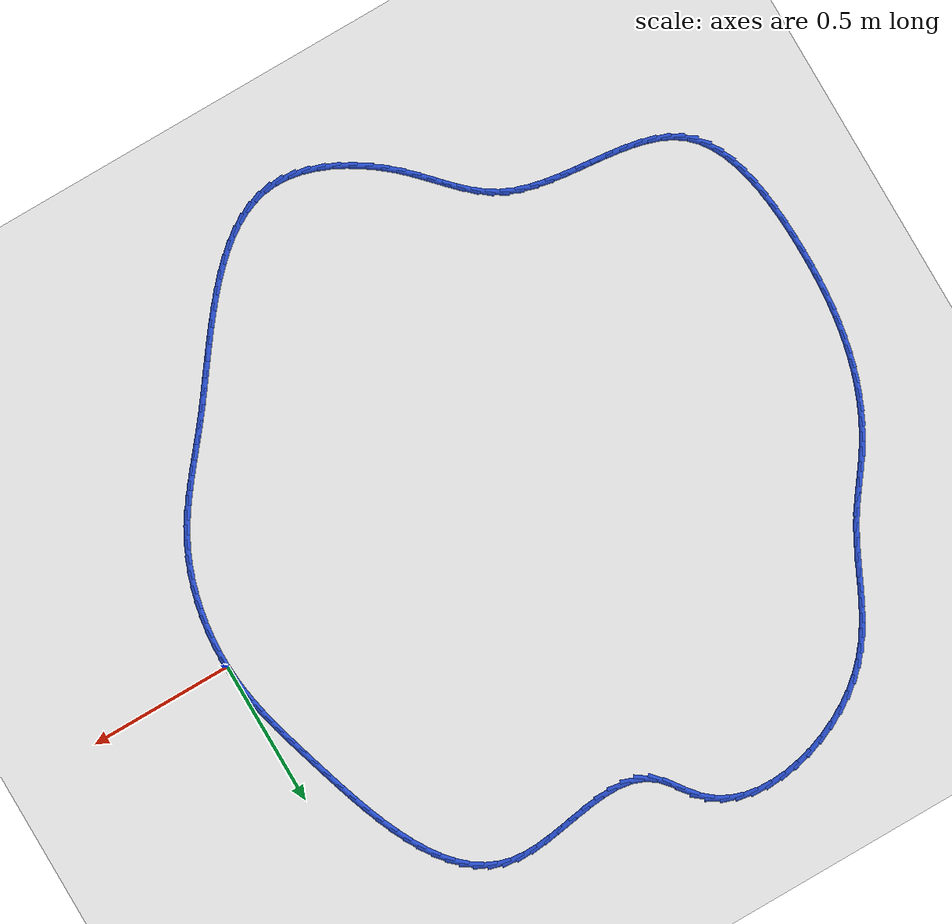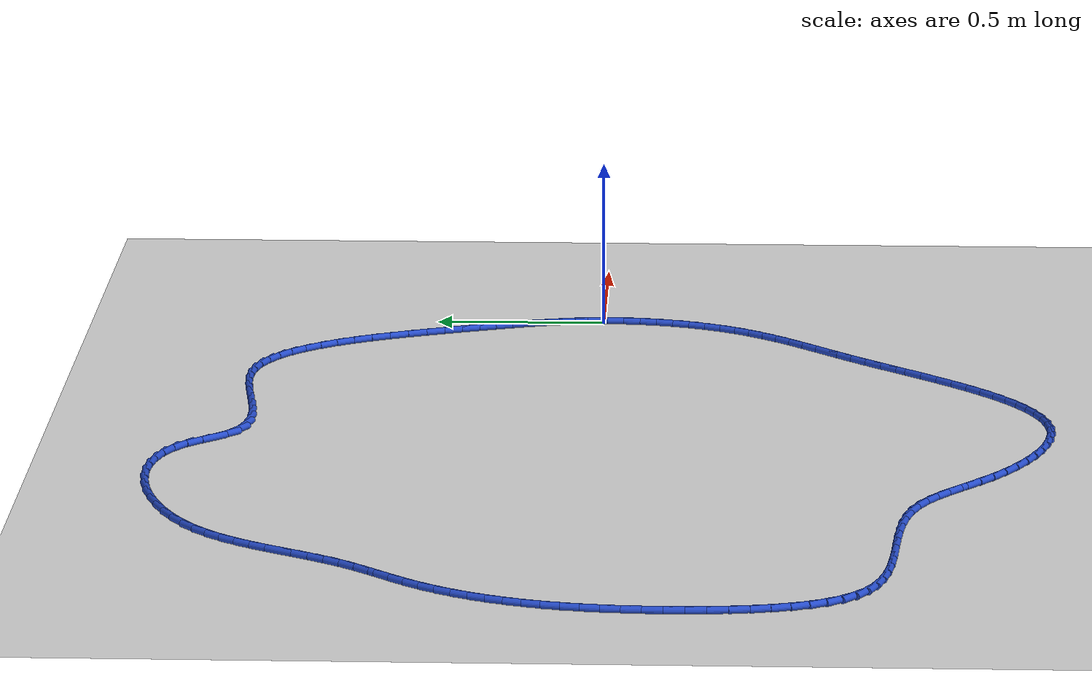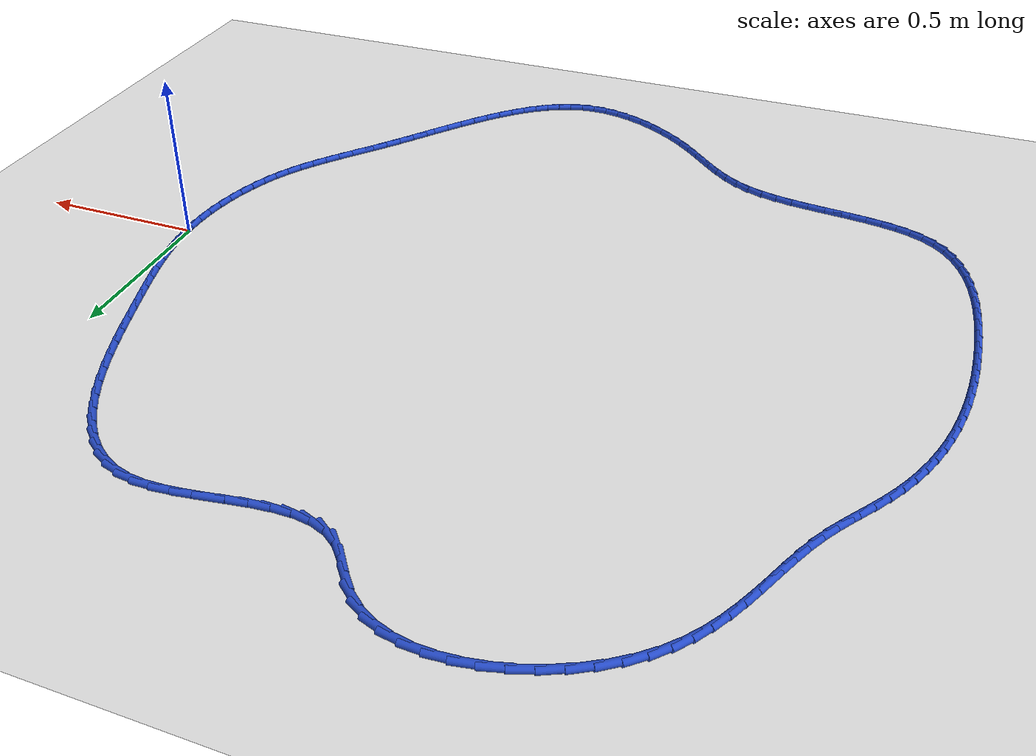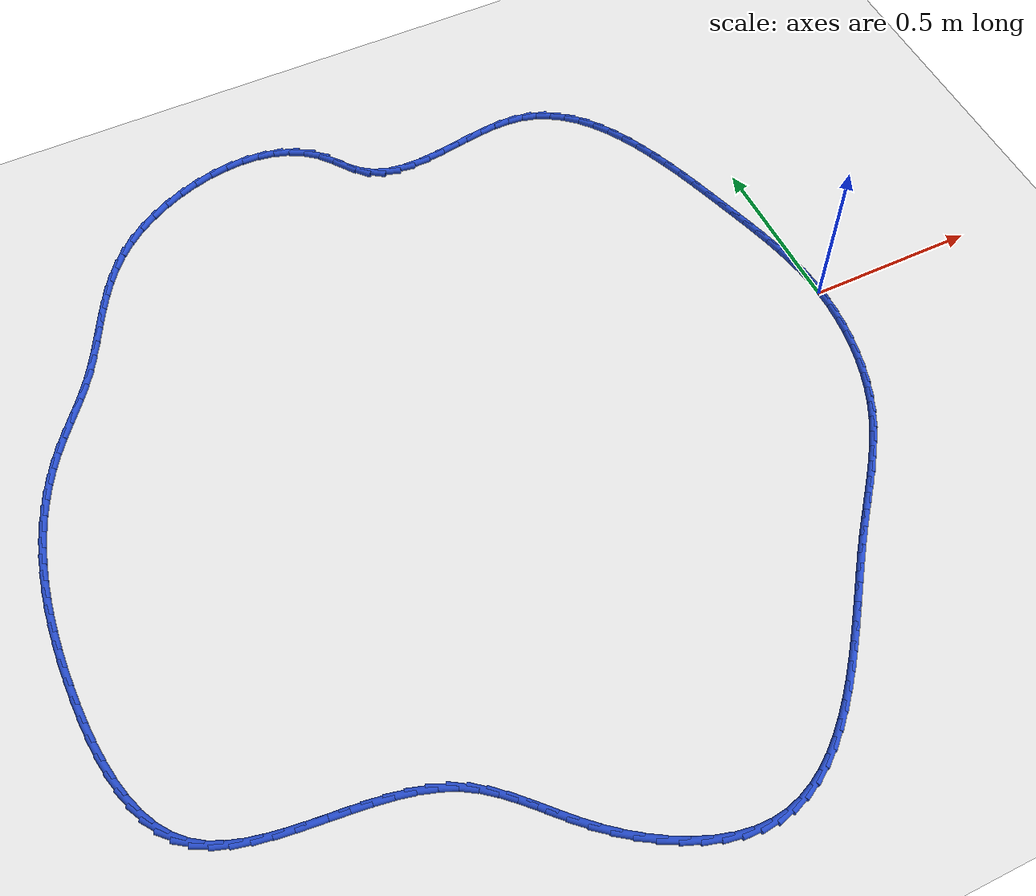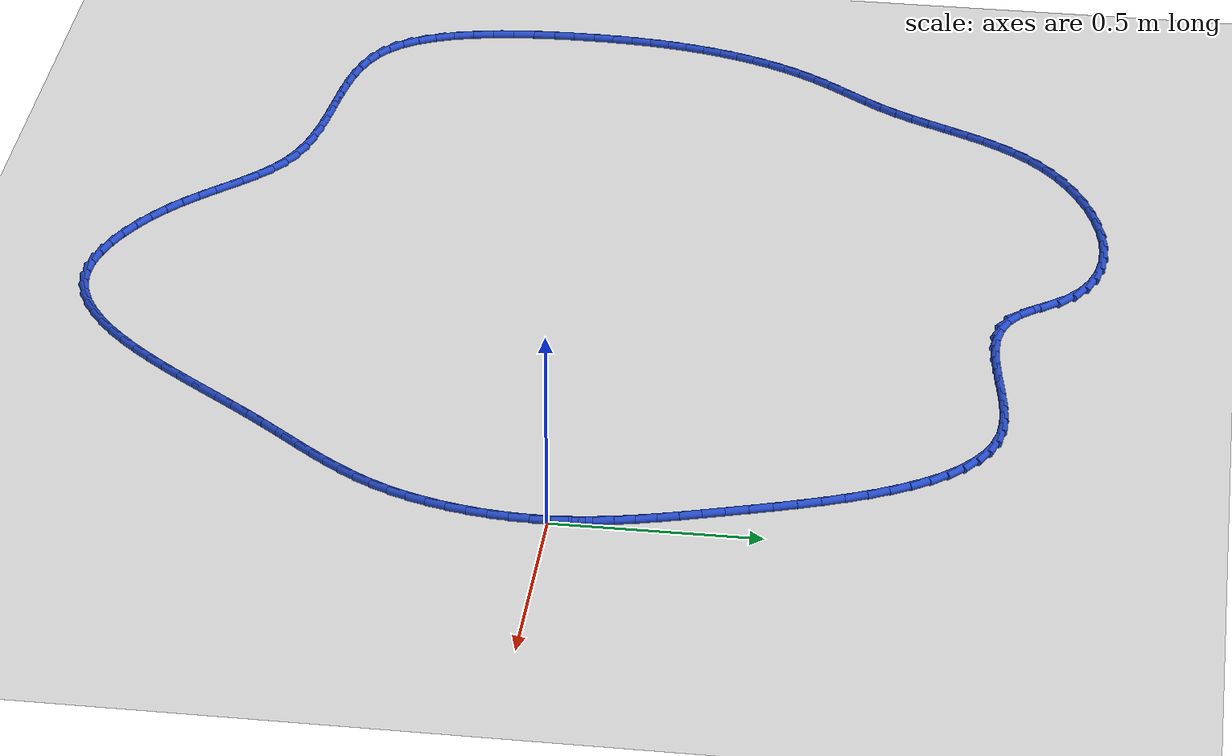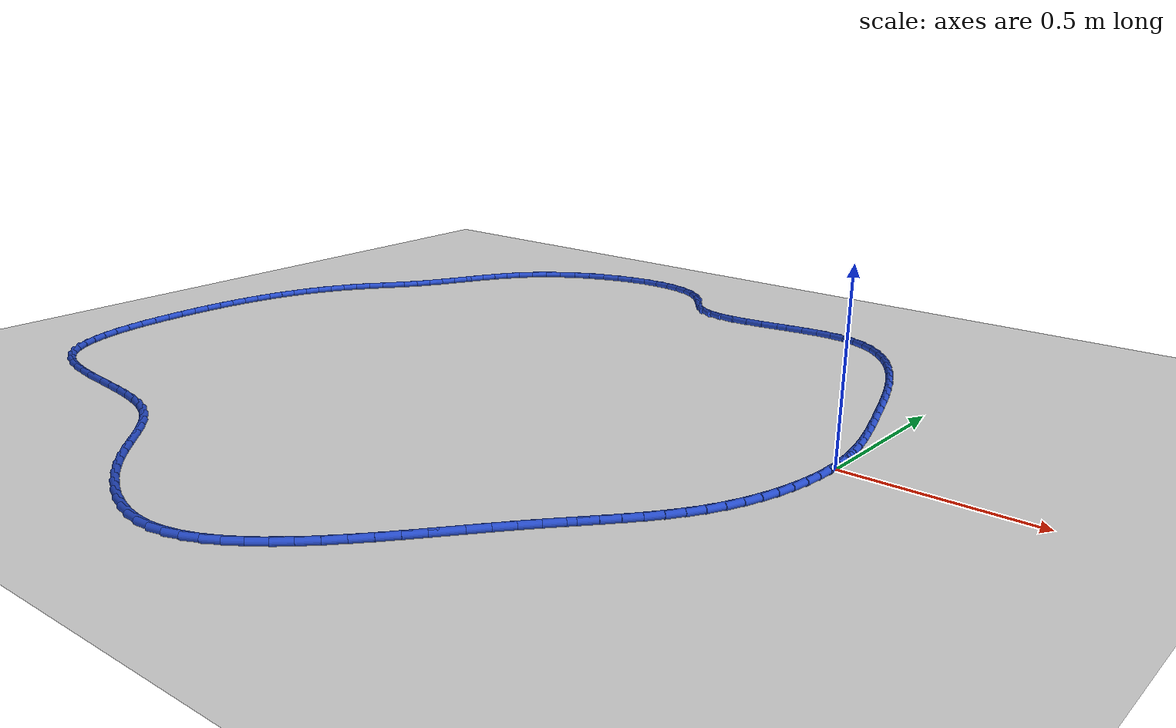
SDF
<sdf version="1.6">
 <world name="default">
  <light name="sun" type="directional">
   <pose>0 0 10 0 -0 0</pose>
   <diffuse>0.8 0.8 0.8 1</diffuse>
   <specular>0.2 0.2 0.2 1</specular>
   <attenuation>
    <range>1000</range>
    <constant>0.9</constant>
    <linear>0.01</linear>
    <quadratic>0.001</quadratic>
   </attenuation>
   <direction>-0.5 0.1 -0.9</direction>
  </light>
  <model name="ground_plane">
   <static>1</static>
   <link name="link">
    <collision name="collision">
     <geometry><plane><normal>0 0 1</normal><size>100 100</size></plane></geometry>
     <surface><friction><ode><mu>100</mu><mu2>50</mu2></ode></friction></surface>
    </collision>
    <visual name="visual">
     <cast_shadows>0</cast_shadows>
     <geometry><plane><normal>0 0 1</normal><size>100 100</size></plane></geometry>
     <material>
      <script><uri>file://media/materials/scripts/gazebo.material</uri><name>Gazebo/WhiteGlow</name></script>
     </material>
    </visual>
   </link>
  </model>
  <gravity>0 0 -9.8</gravity>
  <magnetic_field>6e-06 2.3e-05 -4.2e-05</magnetic_field>
  <atmosphere type="adiabatic"/>
  <physics name="default_physics" default="0" type="ode">
   <max_step_size>0.001</max_step_size>
   <real_time_factor>1</real_time_factor>
   <real_time_update_rate>1000</real_time_update_rate>
  </physics>
  <scene><ambient>0.4 0.4 0.4 1</ambient><background>0.7 0.7 0.7 1</background><shadows>1</shadows></scene>
  <spherical_coordinates>
   <surface_model>EARTH_WGS84</surface_model>
   <latitude_deg>0</latitude_deg>
   <longitude_deg>0</longitude_deg>
   <elevation>0</elevation>
   <heading_deg>0</heading_deg>
  </spherical_coordinates>
  <model name="line">
   <link name="link_0">
    <pose>8.673617379884035e-18 -4.163336342344337e-17 0.01 0 1.57 -1.5116043628234455</pose>
    <collision name="collision">
     <geometry><cylinder><radius>0.01</radius><length>0.08</length></cylinder></geometry>
    </collision>
    <visual name="visual">
     <material>
      <script><name>Gazebo/Blue</name><uri>file://media/materials/scripts/gazebo.material</uri></script>
     </material>
     <geometry><cylinder><radius>0.01</radius><length>0.08</length></cylinder></geometry>
    </visual>
   </link>
   <link name="link_1">
    <pose>-0.0028596655203615533 0.04825528257314192 0.01 0 1.57 -1.456718568302291</pose>
    <collision name="collision">
     <geometry><cylinder><radius>0.01</radius><length>0.08</length></cylinder></geometry>
    </collision>
    <visual name="visual">
     <material>
      <script><name>Gazebo/Blue</name><uri>file://media/materials/scripts/gazebo.material</uri></script>
     </material>
     <geometry><cylinder><radius>0.01</radius><length>0.08</length></cylinder></geometry>
    </visual>
   </link>
   <link name="link_2">
    <pose>-0.008313842283554697 0.09585874661139786 0.01 0 1.57 -1.4078513970397568</pose>
    <collision name="collision">
     <geometry><cylinder><radius>0.01</radius><length>0.08</length></cylinder></geometry>
    </collision>
    <visual name="visual">
     <material>
      <script><name>Gazebo/Blue</name><uri>file://media/materials/scripts/gazebo.material</uri></script>
     </material>
     <geometry><cylinder><radius>0.01</radius><length>0.08</length></cylinder></geometry>
    </visual>
   </link>
   <link name="link_3">
    <pose>-0.016084770692792957 0.14312643967942 0.01 0 1.57 -1.3660786692983289</pose>
    <collision name="collision">
     <geometry><cylinder><radius>0.01</radius><length>0.08</length></cylinder></geometry>
    </collision>
    <visual name="visual">
     <material>
      <script><name>Gazebo/Blue</name><uri>file://media/materials/scripts/gazebo.material</uri></script>
     </material>
     <geometry><cylinder><radius>0.01</radius><length>0.08</length></cylinder></geometry>
    </visual>
   </link>
   <link name="link_4">
    <pose>-0.02589469115128985 0.1903744093418604 0.01 0 1.57 -1.3320614121022025</pose>
    <collision name="collision">
     <geometry><cylinder><radius>0.01</radius><length>0.08</length></cylinder></geometry>
    </collision>
    <visual name="visual">
     <material>
      <script><name>Gazebo/Blue</name><uri>file://media/materials/scripts/gazebo.material</uri></script>
     </material>
     <geometry><cylinder><radius>0.01</radius><length>0.08</length></cylinder></geometry>
    </visual>
   </link>
   <link name="link_5">
    <pose>-0.03746584406225891 0.23791870316337138 0.01 0 1.57 -1.3060720190467154</pose>
    <collision name="collision">
     <geometry><cylinder><radius>0.01</radius><length>0.08</length></cylinder></geometry>
    </collision>
    <visual name="visual">
     <material>
      <script><name>Gazebo/Blue</name><uri>file://media/materials/scripts/gazebo.material</uri></script>
     </material>
     <geometry><cylinder><radius>0.01</radius><length>0.08</length></cylinder></geometry>
    </visual>
   </link>
   <link name="link_6">
    <pose>-0.05052046982891368 0.28607536870860506 0.01 0 1.57 -1.2880566774438684</pose>
    <collision name="collision">
     <geometry><cylinder><radius>0.01</radius><length>0.08</length></cylinder></geometry>
    </collision>
    <visual name="visual">
     <material>
      <script><name>Gazebo/Blue</name><uri>file://media/materials/scripts/gazebo.material</uri></script>
     </material>
     <geometry><cylinder><radius>0.01</radius><length>0.08</length></cylinder></geometry>
    </visual>
   </link>
   <link name="link_7">
    <pose>-0.06478080885446766 0.3351604535422136 0.01 0 1.57 -1.2777102090251995</pose>
    <collision name="collision">
     <geometry><cylinder><radius>0.01</radius><length>0.08</length></cylinder></geometry>
    </collision>
    <visual name="visual">
     <material>
      <script><name>Gazebo/Blue</name><uri>file://media/materials/scripts/gazebo.material</uri></script>
     </material>
     <geometry><cylinder><radius>0.01</radius><length>0.08</length></cylinder></geometry>
    </visual>
   </link>
   <link name="link_8">
    <pose>-0.07996910154213442 0.38549000522884913 0.01 0 1.57 -1.274079964308338</pose>
    <collision name="collision">
     <geometry><cylinder><radius>0.01</radius><length>0.08</length></cylinder></geometry>
    </collision>
    <visual name="visual">
     <material>
      <script><name>Gazebo/Blue</name><uri>file://media/materials/scripts/gazebo.material</uri></script>
     </material>
     <geometry><cylinder><radius>0.01</radius><length>0.08</length></cylinder></geometry>
    </visual>
   </link>
   <link name="link_9">
    <pose>-0.09582421700834413 0.43734782415424683 0.01 0 1.57 -1.2694433381980668</pose>
    <collision name="collision">
     <geometry><cylinder><radius>0.01</radius><length>0.08</length></cylinder></geometry>
    </collision>
    <visual name="visual">
     <material>
      <script><name>Gazebo/Blue</name><uri>file://media/materials/scripts/gazebo.material</uri></script>
     </material>
     <geometry><cylinder><radius>0.01</radius><length>0.08</length></cylinder></geometry>
    </visual>
   </link>
   <link name="link_10">
    <pose>-0.11234759132022659 0.49050852858483596 0.01 0 1.57 -1.258127386948987</pose>
    <collision name="collision">
     <geometry><cylinder><radius>0.01</radius><length>0.08</length></cylinder></geometry>
    </collision>
    <visual name="visual">
     <material>
      <script><name>Gazebo/Blue</name><uri>file://media/materials/scripts/gazebo.material</uri></script>
     </material>
     <geometry><cylinder><radius>0.01</radius><length>0.08</length></cylinder></geometry>
    </visual>
   </link>
   <link name="link_11">
    <pose>-0.12975005790977417 0.54434066361701 0.01 0 1.57 -1.2399732455387567</pose>
    <collision name="collision">
     <geometry><cylinder><radius>0.01</radius><length>0.08</length></cylinder></geometry>
    </collision>
    <visual name="visual">
     <material>
      <script><name>Gazebo/Blue</name><uri>file://media/materials/scripts/gazebo.material</uri></script>
     </material>
     <geometry><cylinder><radius>0.01</radius><length>0.08</length></cylinder></geometry>
    </visual>
   </link>
   <link name="link_12">
    <pose>-0.14824827404152657 0.5982014804985214 0.01 0 1.57 -1.2146116648747454</pose>
    <collision name="collision">
     <geometry><cylinder><radius>0.01</radius><length>0.08</length></cylinder></geometry>
    </collision>
    <visual name="visual">
     <material>
      <script><name>Gazebo/Blue</name><uri>file://media/materials/scripts/gazebo.material</uri></script>
     </material>
     <geometry><cylinder><radius>0.01</radius><length>0.08</length></cylinder></geometry>
    </visual>
   </link>
   <link name="link_13">
    <pose>-0.16805889698002344 0.6514482304771235 0.01 0 1.57 -1.1813070271315929</pose>
    <collision name="collision">
     <geometry><cylinder><radius>0.01</radius><length>0.08</length></cylinder></geometry>
    </collision>
    <visual name="visual">
     <material>
      <script><name>Gazebo/Blue</name><uri>file://media/materials/scripts/gazebo.material</uri></script>
     </material>
     <geometry><cylinder><radius>0.01</radius><length>0.08</length></cylinder></geometry>
    </visual>
   </link>
   <link name="link_14">
    <pose>-0.18939858398980458 0.7034381648005698 0.01 0 1.57 -1.1389354904783646</pose>
    <collision name="collision">
     <geometry><cylinder><radius>0.01</radius><length>0.08</length></cylinder></geometry>
    </collision>
    <visual name="visual">
     <material>
      <script><name>Gazebo/Blue</name><uri>file://media/materials/scripts/gazebo.material</uri></script>
     </material>
     <geometry><cylinder><radius>0.01</radius><length>0.08</length></cylinder></geometry>
    </visual>
   </link>
   <link name="link_15">
    <pose>-0.2124839923354097 0.7535285347166131 0.01 0 1.57 -1.0859480123321694</pose>
    <collision name="collision">
     <geometry><cylinder><radius>0.01</radius><length>0.08</length></cylinder></geometry>
    </collision>
    <visual name="visual">
     <material>
      <script><name>Gazebo/Blue</name><uri>file://media/materials/scripts/gazebo.material</uri></script>
     </material>
     <geometry><cylinder><radius>0.01</radius><length>0.08</length></cylinder></geometry>
    </visual>
   </link>
   <link name="link_16">
    <pose>-0.2375317792813785 0.8010765914730066 0.01 0 1.57 -1.0203436368515724</pose>
    <collision name="collision">
     <geometry><cylinder><radius>0.01</radius><length>0.08</length></cylinder></geometry>
    </collision>
    <visual name="visual">
     <material>
      <script><name>Gazebo/Blue</name><uri>file://media/materials/scripts/gazebo.material</uri></script>
     </material>
     <geometry><cylinder><radius>0.01</radius><length>0.08</length></cylinder></geometry>
    </visual>
   </link>
   <link name="link_17">
    <pose>-0.26475860209225066 0.8454395863175032 0.01 0 1.57 -0.9397064769150355</pose>
    <collision name="collision">
     <geometry><cylinder><radius>0.01</radius><length>0.08</length></cylinder></geometry>
    </collision>
    <visual name="visual">
     <material>
      <script><name>Gazebo/Blue</name><uri>file://media/materials/scripts/gazebo.material</uri></script>
     </material>
     <geometry><cylinder><radius>0.01</radius><length>0.08</length></cylinder></geometry>
    </visual>
   </link>
   <link name="link_18">
    <pose>-0.294381118032566 0.8859747704978566 0.01 0 1.57 -0.8414125216707599</pose>
    <collision name="collision">
     <geometry><cylinder><radius>0.01</radius><length>0.08</length></cylinder></geometry>
    </collision>
    <visual name="visual">
     <material>
      <script><name>Gazebo/Blue</name><uri>file://media/materials/scripts/gazebo.material</uri></script>
     </material>
     <geometry><cylinder><radius>0.01</radius><length>0.08</length></cylinder></geometry>
    </visual>
   </link>
   <link name="link_19">
    <pose>-0.326615984366864 0.9220393952618191 0.01 0 1.57 -0.7231814292182548</pose>
    <collision name="collision">
     <geometry><cylinder><radius>0.01</radius><length>0.08</length></cylinder></geometry>
    </collision>
    <visual name="visual">
     <material>
      <script><name>Gazebo/Blue</name><uri>file://media/materials/scripts/gazebo.material</uri></script>
     </material>
     <geometry><cylinder><radius>0.01</radius><length>0.08</length></cylinder></geometry>
    </visual>
   </link>
   <link name="link_20">
    <pose>-0.3616798583596846 0.9529907118571445 0.01 0 1.57 -0.5841579033929195</pose>
    <collision name="collision">
     <geometry><cylinder><radius>0.01</radius><length>0.08</length></cylinder></geometry>
    </collision>
    <visual name="visual">
     <material>
      <script><name>Gazebo/Blue</name><uri>file://media/materials/scripts/gazebo.material</uri></script>
     </material>
     <geometry><cylinder><radius>0.01</radius><length>0.08</length></cylinder></geometry>
    </visual>
   </link>
   <link name="link_21">
    <pose>-0.3997893972755676 0.9781859715315858 0.01 0 1.57 -0.42644844307682833</pose>
    <collision name="collision">
     <geometry><cylinder><radius>0.01</radius><length>0.08</length></cylinder></geometry>
    </collision>
    <visual name="visual">
     <material>
      <script><name>Gazebo/Blue</name><uri>file://media/materials/scripts/gazebo.material</uri></script>
     </material>
     <geometry><cylinder><radius>0.01</radius><length>0.08</length></cylinder></geometry>
    </visual>
   </link>
   <link name="link_22">
    <pose>-0.44116125837905246 0.9969824255328961 0.01 0 1.57 -0.2563235282814316</pose>
    <collision name="collision">
     <geometry><cylinder><radius>0.01</radius><length>0.08</length></cylinder></geometry>
    </collision>
    <visual name="visual">
     <material>
      <script><name>Gazebo/Blue</name><uri>file://media/materials/scripts/gazebo.material</uri></script>
     </material>
     <geometry><cylinder><radius>0.01</radius><length>0.08</length></cylinder></geometry>
    </visual>
   </link>
   <link name="link_23">
    <pose>-0.4860120989346792 1.0087373251088285 0.01 0 1.57 -0.09017680046027902</pose>
    <collision name="collision">
     <geometry><cylinder><radius>0.01</radius><length>0.08</length></cylinder></geometry>
    </collision>
    <visual name="visual">
     <material>
      <script><name>Gazebo/Blue</name><uri>file://media/materials/scripts/gazebo.material</uri></script>
     </material>
     <geometry><cylinder><radius>0.01</radius><length>0.08</length></cylinder></geometry>
    </visual>
   </link>
   <link name="link_24">
    <pose>-0.5344193644499591 1.013114408472004 0.01 0 1.57 0.03327140573761685</pose>
    <collision name="collision">
     <geometry><cylinder><radius>0.01</radius><length>0.08</length></cylinder></geometry>
    </collision>
    <visual name="visual">
     <material>
      <script><name>Gazebo/Blue</name><uri>file://media/materials/scripts/gazebo.material</uri></script>
     </material>
     <geometry><cylinder><radius>0.01</radius><length>0.08</length></cylinder></geometry>
    </visual>
   </link>
   <link name="link_25">
    <pose>-0.5857203490060683 1.0114069224989901 0.01 0 1.57 0.11137271273972658</pose>
    <collision name="collision">
     <geometry><cylinder><radius>0.01</radius><length>0.08</length></cylinder></geometry>
    </collision>
    <visual name="visual">
     <material>
      <script><name>Gazebo/Blue</name><uri>file://media/materials/scripts/gazebo.material</uri></script>
     </material>
     <geometry><cylinder><radius>0.01</radius><length>0.08</length></cylinder></geometry>
    </visual>
   </link>
   <link name="link_26">
    <pose>-0.6390073267635895 1.0054475470380935 0.01 0 1.57 0.1529076866029552</pose>
    <collision name="collision">
     <geometry><cylinder><radius>0.01</radius><length>0.08</length></cylinder></geometry>
    </collision>
    <visual name="visual">
     <material>
      <script><name>Gazebo/Blue</name><uri>file://media/materials/scripts/gazebo.material</uri></script>
     </material>
     <geometry><cylinder><radius>0.01</radius><length>0.08</length></cylinder></geometry>
    </visual>
   </link>
   <link name="link_27">
    <pose>-0.6933724143653721 0.9970693087268081 0.01 0 1.57 0.16291512776615355</pose>
    <collision name="collision">
     <geometry><cylinder><radius>0.01</radius><length>0.08</length></cylinder></geometry>
    </collision>
    <visual name="visual">
     <material>
      <script><name>Gazebo/Blue</name><uri>file://media/materials/scripts/gazebo.material</uri></script>
     </material>
     <geometry><cylinder><radius>0.01</radius><length>0.08</length></cylinder></geometry>
    </visual>
   </link>
   <link name="link_28">
    <pose>-0.7479077284542658 0.9881052342026269 0.01 0 1.57 0.1424709062198668</pose>
    <collision name="collision">
     <geometry><cylinder><radius>0.01</radius><length>0.08</length></cylinder></geometry>
    </collision>
    <visual name="visual">
     <material>
      <script><name>Gazebo/Blue</name><uri>file://media/materials/scripts/gazebo.material</uri></script>
     </material>
     <geometry><cylinder><radius>0.01</radius><length>0.08</length></cylinder></geometry>
    </visual>
   </link>
   <link name="link_29">
    <pose>-0.8017053856731208 0.9803883501030435 0.01 0 1.57 0.08867344712582415</pose>
    <collision name="collision">
     <geometry><cylinder><radius>0.01</radius><length>0.08</length></cylinder></geometry>
    </collision>
    <visual name="visual">
     <material>
      <script><name>Gazebo/Blue</name><uri>file://media/materials/scripts/gazebo.material</uri></script>
     </material>
     <geometry><cylinder><radius>0.01</radius><length>0.08</length></cylinder></geometry>
    </visual>
   </link>
   <link name="link_30">
    <pose>-0.8538575026647859 0.9757516830655513 0.01 0 1.57 -0.005576231477649407</pose>
    <collision name="collision">
     <geometry><cylinder><radius>0.01</radius><length>0.08</length></cylinder></geometry>
    </collision>
    <visual name="visual">
     <material>
      <script><name>Gazebo/Blue</name><uri>file://media/materials/scripts/gazebo.material</uri></script>
     </material>
     <geometry><cylinder><radius>0.01</radius><length>0.08</length></cylinder></geometry>
    </visual>
   </link>
   <link name="link_31">
    <pose>-0.9034561960721113 0.9760282597276433 0.01 0 1.57 -0.1510564470130311</pose>
    <collision name="collision">
     <geometry><cylinder><radius>0.01</radius><length>0.08</length></cylinder></geometry>
    </collision>
    <visual name="visual">
     <material>
      <script><name>Gazebo/Blue</name><uri>file://media/materials/scripts/gazebo.material</uri></script>
     </material>
     <geometry><cylinder><radius>0.01</radius><length>0.08</length></cylinder></geometry>
    </visual>
   </link>
   <link name="link_32">
    <pose>-0.949593582537946 0.9830511067268131 0.01 0 1.57 -0.3574911483254432</pose>
    <collision name="collision">
     <geometry><cylinder><radius>0.01</radius><length>0.08</length></cylinder></geometry>
    </collision>
    <visual name="visual">
     <material>
      <script><name>Gazebo/Blue</name><uri>file://media/materials/scripts/gazebo.material</uri></script>
     </material>
     <geometry><cylinder><radius>0.01</radius><length>0.08</length></cylinder></geometry>
    </visual>
   </link>
   <link name="link_33">
    <pose>-0.9913617787051403 0.9986532507005537 0.01 0 1.57 -0.6193011846903569</pose>
    <collision name="collision">
     <geometry><cylinder><radius>0.01</radius><length>0.08</length></cylinder></geometry>
    </collision>
    <visual name="visual">
     <material>
      <script><name>Gazebo/Blue</name><uri>file://media/materials/scripts/gazebo.material</uri></script>
     </material>
     <geometry><cylinder><radius>0.01</radius><length>0.08</length></cylinder></geometry>
    </visual>
   </link>
   <link name="link_34">
    <pose>-1.0278535531143147 1.024666578300198 0.01 0 1.57 -0.8583462180130956</pose>
    <collision name="collision">
     <geometry><cylinder><radius>0.01</radius><length>0.08</length></cylinder></geometry>
    </collision>
    <visual name="visual">
     <material>
      <script><name>Gazebo/Blue</name><uri>file://media/materials/scripts/gazebo.material</uri></script>
     </material>
     <geometry><cylinder><radius>0.01</radius><length>0.08</length></cylinder></geometry>
    </visual>
   </link>
   <link name="link_35">
    <pose>-1.0592521466866684 1.0610160461672293 0.01 0 1.57 -0.9399554776087398</pose>
    <collision name="collision">
     <geometry><cylinder><radius>0.01</radius><length>0.08</length></cylinder></geometry>
    </collision>
    <visual name="visual">
     <material>
      <script><name>Gazebo/Blue</name><uri>file://media/materials/scripts/gazebo.material</uri></script>
     </material>
     <geometry><cylinder><radius>0.01</radius><length>0.08</length></cylinder></geometry>
    </visual>
   </link>
   <link name="link_36">
    <pose>-1.0890587462248686 1.1018244552121772 0.01 0 1.57 -0.8694432912183789</pose>
    <collision name="collision">
     <geometry><cylinder><radius>0.01</radius><length>0.08</length></cylinder></geometry>
    </collision>
    <visual name="visual">
     <material>
      <script><name>Gazebo/Blue</name><uri>file://media/materials/scripts/gazebo.material</uri></script>
     </material>
     <geometry><cylinder><radius>0.01</radius><length>0.08</length></cylinder></geometry>
    </visual>
   </link>
   <link name="link_37">
    <pose>-1.1214014624738773 1.140117806307576 0.01 0 1.57 -0.6801421170573124</pose>
    <collision name="collision">
     <geometry><cylinder><radius>0.01</radius><length>0.08</length></cylinder></geometry>
    </collision>
    <visual name="visual">
     <material>
      <script><name>Gazebo/Blue</name><uri>file://media/materials/scripts/gazebo.material</uri></script>
     </material>
     <geometry><cylinder><radius>0.01</radius><length>0.08</length></cylinder></geometry>
    </visual>
   </link>
   <link name="link_38">
    <pose>-1.1592090393875638 1.170700221218077 0.01 0 1.57 -0.4831215529222764</pose>
    <collision name="collision">
     <geometry><cylinder><radius>0.01</radius><length>0.08</length></cylinder></geometry>
    </collision>
    <visual name="visual">
     <material>
      <script><name>Gazebo/Blue</name><uri>file://media/materials/scripts/gazebo.material</uri></script>
     </material>
     <geometry><cylinder><radius>0.01</radius><length>0.08</length></cylinder></geometry>
    </visual>
   </link>
   <link name="link_39">
    <pose>-1.2021414602996265 1.1932219218281757 0.01 0 1.57 -0.3065482753140255</pose>
    <collision name="collision">
     <geometry><cylinder><radius>0.01</radius><length>0.08</length></cylinder></geometry>
    </collision>
    <visual name="visual">
     <material>
      <script><name>Gazebo/Blue</name><uri>file://media/materials/scripts/gazebo.material</uri></script>
     </material>
     <geometry><cylinder><radius>0.01</radius><length>0.08</length></cylinder></geometry>
    </visual>
   </link>
   <link name="link_40">
    <pose>-1.2493070188444522 1.2081510374278424 0.01 0 1.57 -0.15331371193521254</pose>
    <collision name="collision">
     <geometry><cylinder><radius>0.01</radius><length>0.08</length></cylinder></geometry>
    </collision>
    <visual name="visual">
     <material>
      <script><name>Gazebo/Blue</name><uri>file://media/materials/scripts/gazebo.material</uri></script>
     </material>
     <geometry><cylinder><radius>0.01</radius><length>0.08</length></cylinder></geometry>
    </visual>
   </link>
   <link name="link_41">
    <pose>-1.2998140086564274 1.2159556973070471 0.01 0 1.57 -0.021680980756804104</pose>
    <collision name="collision">
     <geometry><cylinder><radius>0.01</radius><length>0.08</length></cylinder></geometry>
    </collision>
    <visual name="visual">
     <material>
      <script><name>Gazebo/Blue</name><uri>file://media/materials/scripts/gazebo.material</uri></script>
     </material>
     <geometry><cylinder><radius>0.01</radius><length>0.08</length></cylinder></geometry>
    </visual>
   </link>
   <link name="link_42">
    <pose>-1.352770723369938 1.2171040307557592 0.01 0 1.57 0.09218752684752034</pose>
    <collision name="collision">
     <geometry><cylinder><radius>0.01</radius><length>0.08</length></cylinder></geometry>
    </collision>
    <visual name="visual">
     <material>
      <script><name>Gazebo/Blue</name><uri>file://media/materials/scripts/gazebo.material</uri></script>
     </material>
     <geometry><cylinder><radius>0.01</radius><length>0.08</length></cylinder></geometry>
    </visual>
   </link>
   <link name="link_43">
    <pose>-1.4072854566193707 1.212064167063949 0.01 0 1.57 0.19257677746905266</pose>
    <collision name="collision">
     <geometry><cylinder><radius>0.01</radius><length>0.08</length></cylinder></geometry>
    </collision>
    <visual name="visual">
     <material>
      <script><name>Gazebo/Blue</name><uri>file://media/materials/scripts/gazebo.material</uri></script>
     </material>
     <geometry><cylinder><radius>0.01</radius><length>0.08</length></cylinder></geometry>
    </visual>
   </link>
   <link name="link_44">
    <pose>-1.462466502039111 1.2013042355215848 0.01 0 1.57 0.28351132039232285</pose>
    <collision name="collision">
     <geometry><cylinder><radius>0.01</radius><length>0.08</length></cylinder></geometry>
    </collision>
    <visual name="visual">
     <material>
      <script><name>Gazebo/Blue</name><uri>file://media/materials/scripts/gazebo.material</uri></script>
     </material>
     <geometry><cylinder><radius>0.01</radius><length>0.08</length></cylinder></geometry>
    </visual>
   </link>
   <link name="link_45">
    <pose>-1.5174221532635468 1.185292365418638 0.01 0 1.57 0.3686057370730551</pose>
    <collision name="collision">
     <geometry><cylinder><radius>0.01</radius><length>0.08</length></cylinder></geometry>
    </collision>
    <visual name="visual">
     <material>
      <script><name>Gazebo/Blue</name><uri>file://media/materials/scripts/gazebo.material</uri></script>
     </material>
     <geometry><cylinder><radius>0.01</radius><length>0.08</length></cylinder></geometry>
    </visual>
   </link>
   <link name="link_46">
    <pose>-1.5712607039270623 1.1644966860450774 0.01 0 1.57 0.4511685297060466</pose>
    <collision name="collision">
     <geometry><cylinder><radius>0.01</radius><length>0.08</length></cylinder></geometry>
    </collision>
    <visual name="visual">
     <material>
      <script><name>Gazebo/Blue</name><uri>file://media/materials/scripts/gazebo.material</uri></script>
     </material>
     <geometry><cylinder><radius>0.01</radius><length>0.08</length></cylinder></geometry>
    </visual>
   </link>
   <link name="link_47">
    <pose>-1.6230904476640458 1.1393853266908733 0.01 0 1.57 0.5344074956620822</pose>
    <collision name="collision">
     <geometry><cylinder><radius>0.01</radius><length>0.08</length></cylinder></geometry>
    </collision>
    <visual name="visual">
     <material>
      <script><name>Gazebo/Blue</name><uri>file://media/materials/scripts/gazebo.material</uri></script>
     </material>
     <geometry><cylinder><radius>0.01</radius><length>0.08</length></cylinder></geometry>
    </visual>
   </link>
   <link name="link_48">
    <pose>-1.6720196781088825 1.1104264166459952 0.01 0 1.57 0.6216799573938817</pose>
    <collision name="collision">
     <geometry><cylinder><radius>0.01</radius><length>0.08</length></cylinder></geometry>
    </collision>
    <visual name="visual">
     <material>
      <script><name>Gazebo/Blue</name><uri>file://media/materials/scripts/gazebo.material</uri></script>
     </material>
     <geometry><cylinder><radius>0.01</radius><length>0.08</length></cylinder></geometry>
    </visual>
   </link>
   <link name="link_49">
    <pose>-1.7171566888959586 1.0780880852004127 0.01 0 1.57 0.7167222215268402</pose>
    <collision name="collision">
     <geometry><cylinder><radius>0.01</radius><length>0.08</length></cylinder></geometry>
    </collision>
    <visual name="visual">
     <material>
      <script><name>Gazebo/Blue</name><uri>file://media/materials/scripts/gazebo.material</uri></script>
     </material>
     <geometry><cylinder><radius>0.01</radius><length>0.08</length></cylinder></geometry>
    </visual>
   </link>
   <link name="link_50">
    <pose>-1.7576139667790667 1.04283825370918 0.01 0 1.57 0.8168830074227434</pose>
    <collision name="collision">
     <geometry><cylinder><radius>0.01</radius><length>0.08</length></cylinder></geometry>
    </collision>
    <visual name="visual">
     <material>
      <script><name>Gazebo/Blue</name><uri>file://media/materials/scripts/gazebo.material</uri></script>
     </material>
     <geometry><cylinder><radius>0.01</radius><length>0.08</length></cylinder></geometry>
    </visual>
   </link>
   <link name="link_51">
    <pose>-1.7930300399470722 1.005118757367901 0.01 0 1.57 0.9083321926003661</pose>
    <collision name="collision">
     <geometry><cylinder><radius>0.01</radius><length>0.08</length></cylinder></geometry>
    </collision>
    <visual name="visual">
     <material>
      <script><name>Gazebo/Blue</name><uri>file://media/materials/scripts/gazebo.material</uri></script>
     </material>
     <geometry><cylinder><radius>0.01</radius><length>0.08</length></cylinder></geometry>
    </visual>
   </link>
   <link name="link_52">
    <pose>-1.8240752884031552 0.9653202623022881 0.01 0 1.57 0.9860888631982911</pose>
    <collision name="collision">
     <geometry><cylinder><radius>0.01</radius><length>0.08</length></cylinder></geometry>
    </collision>
    <visual name="visual">
     <material>
      <script><name>Gazebo/Blue</name><uri>file://media/materials/scripts/gazebo.material</uri></script>
     </material>
     <geometry><cylinder><radius>0.01</radius><length>0.08</length></cylinder></geometry>
    </visual>
   </link>
   <link name="link_53">
    <pose>-1.8515400815448524 0.9238274844176625 0.01 0 1.57 1.0478502974705735</pose>
    <collision name="collision">
     <geometry><cylinder><radius>0.01</radius><length>0.08</length></cylinder></geometry>
    </collision>
    <visual name="visual">
     <material>
      <script><name>Gazebo/Blue</name><uri>file://media/materials/scripts/gazebo.material</uri></script>
     </material>
     <geometry><cylinder><radius>0.01</radius><length>0.08</length></cylinder></geometry>
    </visual>
   </link>
   <link name="link_54">
    <pose>-1.8762147887696987 0.8810251396193443 0.01 0 1.57 1.092414519392502</pose>
    <collision name="collision">
     <geometry><cylinder><radius>0.01</radius><length>0.08</length></cylinder></geometry>
    </collision>
    <visual name="visual">
     <material>
      <script><name>Gazebo/Blue</name><uri>file://media/materials/scripts/gazebo.material</uri></script>
     </material>
     <geometry><cylinder><radius>0.01</radius><length>0.08</length></cylinder></geometry>
    </visual>
   </link>
   <link name="link_55">
    <pose>-1.898889779475232 0.8372979438126558 0.01 0 1.57 1.119293939073383</pose>
    <collision name="collision">
     <geometry><cylinder><radius>0.01</radius><length>0.08</length></cylinder></geometry>
    </collision>
    <visual name="visual">
     <material>
      <script><name>Gazebo/Blue</name><uri>file://media/materials/scripts/gazebo.material</uri></script>
     </material>
     <geometry><cylinder><radius>0.01</radius><length>0.08</length></cylinder></geometry>
    </visual>
   </link>
   <link name="link_56">
    <pose>-1.920355423058988 0.793030612902918 0.01 0 1.57 1.1283428545215968</pose>
    <collision name="collision">
     <geometry><cylinder><radius>0.01</radius><length>0.08</length></cylinder></geometry>
    </collision>
    <visual name="visual">
     <material>
      <script><name>Gazebo/Blue</name><uri>file://media/materials/scripts/gazebo.material</uri></script>
     </material>
     <geometry><cylinder><radius>0.01</radius><length>0.08</length></cylinder></geometry>
    </visual>
   </link>
   <link name="link_57">
    <pose>-1.9414020889185035 0.7486078627954513 0.01 0 1.57 1.1195094449584073</pose>
    <collision name="collision">
     <geometry><cylinder><radius>0.01</radius><length>0.08</length></cylinder></geometry>
    </collision>
    <visual name="visual">
     <material>
      <script><name>Gazebo/Blue</name><uri>file://media/materials/scripts/gazebo.material</uri></script>
     </material>
     <geometry><cylinder><radius>0.01</radius><length>0.08</length></cylinder></geometry>
    </visual>
   </link>
   <link name="link_58">
    <pose>-1.962820146451315 0.7044144093955771 0.01 0 1.57 1.0927500852803989</pose>
    <collision name="collision">
     <geometry><cylinder><radius>0.01</radius><length>0.08</length></cylinder></geometry>
    </collision>
    <visual name="visual">
     <material>
      <script><name>Gazebo/Blue</name><uri>file://media/materials/scripts/gazebo.material</uri></script>
     </material>
     <geometry><cylinder><radius>0.01</radius><length>0.08</length></cylinder></geometry>
    </visual>
   </link>
   <link name="link_59">
    <pose>-1.9853999650549596 0.6608349686086172 0.01 0 1.57 1.048114588843749</pose>
    <collision name="collision">
     <geometry><cylinder><radius>0.01</radius><length>0.08</length></cylinder></geometry>
    </collision>
    <visual name="visual">
     <material>
      <script><name>Gazebo/Blue</name><uri>file://media/materials/scripts/gazebo.material</uri></script>
     </material>
     <geometry><cylinder><radius>0.01</radius><length>0.08</length></cylinder></geometry>
    </visual>
   </link>
   <link name="link_60">
    <pose>-2.009931914126972 0.6182542563398917 0.01 0 1.57 0.9909827484971178</pose>
    <collision name="collision">
     <geometry><cylinder><radius>0.01</radius><length>0.08</length></cylinder></geometry>
    </collision>
    <visual name="visual">
     <material>
      <script><name>Gazebo/Blue</name><uri>file://media/materials/scripts/gazebo.material</uri></script>
     </material>
     <geometry><cylinder><radius>0.01</radius><length>0.08</length></cylinder></geometry>
    </visual>
   </link>
   <link name="link_61">
    <pose>-2.036981251243193 0.5769513812375051 0.01 0 1.57 0.9507061022593876</pose>
    <collision name="collision">
     <geometry><cylinder><radius>0.01</radius><length>0.08</length></cylinder></geometry>
    </collision>
    <visual name="visual">
     <material>
      <script><name>Gazebo/Blue</name><uri>file://media/materials/scripts/gazebo.material</uri></script>
     </material>
     <geometry><cylinder><radius>0.01</radius><length>0.08</length></cylinder></geometry>
    </visual>
   </link>
   <link name="link_62">
    <pose>-2.0658011623294024 0.5365899165805582 0.01 0 1.57 0.9372060497208428</pose>
    <collision name="collision">
     <geometry><cylinder><radius>0.01</radius><length>0.08</length></cylinder></geometry>
    </collision>
    <visual name="visual">
     <material>
      <script><name>Gazebo/Blue</name><uri>file://media/materials/scripts/gazebo.material</uri></script>
     </material>
     <geometry><cylinder><radius>0.01</radius><length>0.08</length></cylinder></geometry>
    </visual>
   </link>
   <link name="link_63">
    <pose>-2.0951707699177327 0.49661103713361604 0.01 0 1.57 0.9502939800866536</pose>
    <collision name="collision">
     <geometry><cylinder><radius>0.01</radius><length>0.08</length></cylinder></geometry>
    </collision>
    <visual name="visual">
     <material>
      <script><name>Gazebo/Blue</name><uri>file://media/materials/scripts/gazebo.material</uri></script>
     </material>
     <geometry><cylinder><radius>0.01</radius><length>0.08</length></cylinder></geometry>
    </visual>
   </link>
   <link name="link_64">
    <pose>-2.123868551301867 0.45645561495895715 0.01 0 1.57 0.9901048696037019</pose>
    <collision name="collision">
     <geometry><cylinder><radius>0.01</radius><length>0.08</length></cylinder></geometry>
    </collision>
    <visual name="visual">
     <material>
      <script><name>Gazebo/Blue</name><uri>file://media/materials/scripts/gazebo.material</uri></script>
     </material>
     <geometry><cylinder><radius>0.01</radius><length>0.08</length></cylinder></geometry>
    </visual>
   </link>
   <link name="link_65">
    <pose>-2.150693639182263 0.41557350689869477 0.01 0 1.57 1.0445207208860667</pose>
    <collision name="collision">
     <geometry><cylinder><radius>0.01</radius><length>0.08</length></cylinder></geometry>
    </collision>
    <visual name="visual">
     <material>
      <script><name>Gazebo/Blue</name><uri>file://media/materials/scripts/gazebo.material</uri></script>
     </material>
     <geometry><cylinder><radius>0.01</radius><length>0.08</length></cylinder></geometry>
    </visual>
   </link>
   <link name="link_66">
    <pose>-2.175035613777686 0.37367140525763776 0.01 0 1.57 1.098842703640261</pose>
    <collision name="collision">
     <geometry><cylinder><radius>0.01</radius><length>0.08</length></cylinder></geometry>
    </collision>
    <visual name="visual">
     <material>
      <script><name>Gazebo/Blue</name><uri>file://media/materials/scripts/gazebo.material</uri></script>
     </material>
     <geometry><cylinder><radius>0.01</radius><length>0.08</length></cylinder></geometry>
    </visual>
   </link>
   <link name="link_67">
    <pose>-2.1969467460106338 0.33074426246234834 0.01 0 1.57 1.1518505495149305</pose>
    <collision name="collision">
     <geometry><cylinder><radius>0.01</radius><length>0.08</length></cylinder></geometry>
    </collision>
    <visual name="visual">
     <material>
      <script><name>Gazebo/Blue</name><uri>file://media/materials/scripts/gazebo.material</uri></script>
     </material>
     <geometry><cylinder><radius>0.01</radius><length>0.08</length></cylinder></geometry>
    </visual>
   </link>
   <link name="link_68">
    <pose>-2.2165144712211697 0.28680232691265733 0.01 0 1.57 1.2031449046796865</pose>
    <collision name="collision">
     <geometry><cylinder><radius>0.01</radius><length>0.08</length></cylinder></geometry>
    </collision>
    <visual name="visual">
     <material>
      <script><name>Gazebo/Blue</name><uri>file://media/materials/scripts/gazebo.material</uri></script>
     </material>
     <geometry><cylinder><radius>0.01</radius><length>0.08</length></cylinder></geometry>
    </visual>
   </link>
   <link name="link_69">
    <pose>-2.2338262247493557 0.2418558470083937 0.01 0 1.57 1.2523871941533664</pose>
    <collision name="collision">
     <geometry><cylinder><radius>0.01</radius><length>0.08</length></cylinder></geometry>
    </collision>
    <visual name="visual">
     <material>
      <script><name>Gazebo/Blue</name><uri>file://media/materials/scripts/gazebo.material</uri></script>
     </material>
     <geometry><cylinder><radius>0.01</radius><length>0.08</length></cylinder></geometry>
    </visual>
   </link>
   <link name="link_70">
    <pose>-2.2489694419352557 0.19591507114938753 0.01 0 1.57 1.2993066222670764</pose>
    <collision name="collision">
     <geometry><cylinder><radius>0.01</radius><length>0.08</length></cylinder></geometry>
    </collision>
    <visual name="visual">
     <material>
      <script><name>Gazebo/Blue</name><uri>file://media/materials/scripts/gazebo.material</uri></script>
     </material>
     <geometry><cylinder><radius>0.01</radius><length>0.08</length></cylinder></geometry>
    </visual>
   </link>
   <link name="link_71">
    <pose>-2.262031558118932 0.14899024773546832 0.01 0 1.57 1.3437017129529398</pose>
    <collision name="collision">
     <geometry><cylinder><radius>0.01</radius><length>0.08</length></cylinder></geometry>
    </collision>
    <visual name="visual">
     <material>
      <script><name>Gazebo/Blue</name><uri>file://media/materials/scripts/gazebo.material</uri></script>
     </material>
     <geometry><cylinder><radius>0.01</radius><length>0.08</length></cylinder></geometry>
    </visual>
   </link>
   <link name="link_72">
    <pose>-2.273100008640448 0.10109162516646636 0.01 0 1.57 1.3854372518461984</pose>
    <collision name="collision">
     <geometry><cylinder><radius>0.01</radius><length>0.08</length></cylinder></geometry>
    </collision>
    <visual name="visual">
     <material>
      <script><name>Gazebo/Blue</name><uri>file://media/materials/scripts/gazebo.material</uri></script>
     </material>
     <geometry><cylinder><radius>0.01</radius><length>0.08</length></cylinder></geometry>
    </visual>
   </link>
   <link name="link_73">
    <pose>-2.2822622288398655 0.05222945184221122 0.01 0 1.57 1.4244378693734112</pose>
    <collision name="collision">
     <geometry><cylinder><radius>0.01</radius><length>0.08</length></cylinder></geometry>
    </collision>
    <visual name="visual">
     <material>
      <script><name>Gazebo/Blue</name><uri>file://media/materials/scripts/gazebo.material</uri></script>
     </material>
     <geometry><cylinder><radius>0.01</radius><length>0.08</length></cylinder></geometry>
    </visual>
   </link>
   <link name="link_74">
    <pose>-2.289605654057249 0.0024139761625326522 0.01 0 1.57 1.4606795866852578</pose>
    <collision name="collision">
     <geometry><cylinder><radius>0.01</radius><length>0.08</length></cylinder></geometry>
    </collision>
    <visual name="visual">
     <material>
      <script><name>Gazebo/Blue</name><uri>file://media/materials/scripts/gazebo.material</uri></script>
     </material>
     <geometry><cylinder><radius>0.01</radius><length>0.08</length></cylinder></geometry>
    </visual>
   </link>
   <link name="link_75">
    <pose>-2.2952177196326606 -0.04834455347273954 0.01 0 1.57 1.4941805088684836</pose>
    <collision name="collision">
     <geometry><cylinder><radius>0.01</radius><length>0.08</length></cylinder></geometry>
    </collision>
    <visual name="visual">
     <material>
      <script><name>Gazebo/Blue</name><uri>file://media/materials/scripts/gazebo.material</uri></script>
     </material>
     <geometry><cylinder><radius>0.01</radius><length>0.08</length></cylinder></geometry>
    </visual>
   </link>
   <link name="link_76">
    <pose>-2.2991858609061624 -0.10003588866377597 0.01 0 1.57 1.5249915904417612</pose>
    <collision name="collision">
     <geometry><cylinder><radius>0.01</radius><length>0.08</length></cylinder></geometry>
    </collision>
    <visual name="visual">
     <material>
      <script><name>Gazebo/Blue</name><uri>file://media/materials/scripts/gazebo.material</uri></script>
     </material>
     <geometry><cylinder><radius>0.01</radius><length>0.08</length></cylinder></geometry>
    </visual>
   </link>
   <link name="link_77">
    <pose>-2.301597513217818 -0.1526497810107465 0.01 0 1.57 1.5531881040737472</pose>
    <collision name="collision">
     <geometry><cylinder><radius>0.01</radius><length>0.08</length></cylinder></geometry>
    </collision>
    <visual name="visual">
     <material>
      <script><name>Gazebo/Blue</name><uri>file://media/materials/scripts/gazebo.material</uri></script>
     </material>
     <geometry><cylinder><radius>0.01</radius><length>0.08</length></cylinder></geometry>
    </visual>
   </link>
   <link name="link_78">
    <pose>-2.3025401119076916 -0.20617598211382038 0.01 0 1.57 -1.5627304790262764</pose>
    <collision name="collision">
     <geometry><cylinder><radius>0.01</radius><length>0.08</length></cylinder></geometry>
    </collision>
    <visual name="visual">
     <material>
      <script><name>Gazebo/Blue</name><uri>file://media/materials/scripts/gazebo.material</uri></script>
     </material>
     <geometry><cylinder><radius>0.01</radius><length>0.08</length></cylinder></geometry>
    </visual>
   </link>
   <link name="link_79">
    <pose>-2.3021010923158443 -0.2606042435731696 0.01 0 1.57 -1.538536192740324</pose>
    <collision name="collision">
     <geometry><cylinder><radius>0.01</radius><length>0.08</length></cylinder></geometry>
    </collision>
    <visual name="visual">
     <material>
      <script><name>Gazebo/Blue</name><uri>file://media/materials/scripts/gazebo.material</uri></script>
     </material>
     <geometry><cylinder><radius>0.01</radius><length>0.08</length></cylinder></geometry>
    </visual>
   </link>
   <link name="link_80">
    <pose>-2.3003182188799167 -0.3158506012462425 0.01 0 1.57 -1.5095007134639327</pose>
    <collision name="collision">
     <geometry><cylinder><radius>0.01</radius><length>0.08</length></cylinder></geometry>
    </collision>
    <visual name="visual">
     <material>
      <script><name>Gazebo/Blue</name><uri>file://media/materials/scripts/gazebo.material</uri></script>
     </material>
     <geometry><cylinder><radius>0.01</radius><length>0.08</length></cylinder></geometry>
    </visual>
   </link>
   <link name="link_81">
    <pose>-2.2969114985297905 -0.3713595124697224 0.01 0 1.57 -1.4723384046299697</pose>
    <collision name="collision">
     <geometry><cylinder><radius>0.01</radius><length>0.08</length></cylinder></geometry>
    </collision>
    <visual name="visual">
     <material>
      <script><name>Gazebo/Blue</name><uri>file://media/materials/scripts/gazebo.material</uri></script>
     </material>
     <geometry><cylinder><radius>0.01</radius><length>0.08</length></cylinder></geometry>
    </visual>
   </link>
   <link name="link_82">
    <pose>-2.291475767520938 -0.4263896709081828 0.01 0 1.57 -1.4255659213302603</pose>
    <collision name="collision">
     <geometry><cylinder><radius>0.01</radius><length>0.08</length></cylinder></geometry>
    </collision>
    <visual name="visual">
     <material>
      <script><name>Gazebo/Blue</name><uri>file://media/materials/scripts/gazebo.material</uri></script>
     </material>
     <geometry><cylinder><radius>0.01</radius><length>0.08</length></cylinder></geometry>
    </visual>
   </link>
   <link name="link_83">
    <pose>-2.283605559723825 -0.4801993214617437 0.01 0 1.57 -1.3670908511453073</pose>
    <collision name="collision">
     <geometry><cylinder><radius>0.01</radius><length>0.08</length></cylinder></geometry>
    </collision>
    <visual name="visual">
     <material>
      <script><name>Gazebo/Blue</name><uri>file://media/materials/scripts/gazebo.material</uri></script>
     </material>
     <geometry><cylinder><radius>0.01</radius><length>0.08</length></cylinder></geometry>
    </visual>
   </link>
   <link name="link_84">
    <pose>-2.2728954090089144 -0.5320467090305278 0.01 0 1.57 -1.2941040796726326</pose>
    <collision name="collision">
     <geometry><cylinder><radius>0.01</radius><length>0.08</length></cylinder></geometry>
    </collision>
    <visual name="visual">
     <material>
      <script><name>Gazebo/Blue</name><uri>file://media/materials/scripts/gazebo.material</uri></script>
     </material>
     <geometry><cylinder><radius>0.01</radius><length>0.08</length></cylinder></geometry>
    </visual>
   </link>
   <link name="link_85">
    <pose>-2.2589398492466737 -0.5811900785146545 0.01 0 1.57 -1.203042413620935</pose>
    <collision name="collision">
     <geometry><cylinder><radius>0.01</radius><length>0.08</length></cylinder></geometry>
    </collision>
    <visual name="visual">
     <material>
      <script><name>Gazebo/Blue</name><uri>file://media/materials/scripts/gazebo.material</uri></script>
     </material>
     <geometry><cylinder><radius>0.01</radius><length>0.08</length></cylinder></geometry>
    </visual>
   </link>
   <link name="link_86">
    <pose>-2.241333414307567 -0.6268876748142465 0.01 0 1.57 -1.0898077549261511</pose>
    <collision name="collision">
     <geometry><cylinder><radius>0.01</radius><length>0.08</length></cylinder></geometry>
    </collision>
    <visual name="visual">
     <material>
      <script><name>Gazebo/Blue</name><uri>file://media/materials/scripts/gazebo.material</uri></script>
     </material>
     <geometry><cylinder><radius>0.01</radius><length>0.08</length></cylinder></geometry>
    </visual>
   </link>
   <link name="link_87">
    <pose>-2.2196706380620608 -0.6683977428294241 0.01 0 1.57 -0.9506291742447966</pose>
    <collision name="collision">
     <geometry><cylinder><radius>0.01</radius><length>0.08</length></cylinder></geometry>
    </collision>
    <visual name="visual">
     <material>
      <script><name>Gazebo/Blue</name><uri>file://media/materials/scripts/gazebo.material</uri></script>
     </material>
     <geometry><cylinder><radius>0.01</radius><length>0.08</length></cylinder></geometry>
    </visual>
   </link>
   <link name="link_88">
    <pose>-2.1935460543806196 -0.7049785274603075 0.01 0 1.57 -0.7840716864156042</pose>
    <collision name="collision">
     <geometry><cylinder><radius>0.01</radius><length>0.08</length></cylinder></geometry>
    </collision>
    <visual name="visual">
     <material>
      <script><name>Gazebo/Blue</name><uri>file://media/materials/scripts/gazebo.material</uri></script>
     </material>
     <geometry><cylinder><radius>0.01</radius><length>0.08</length></cylinder></geometry>
    </visual>
   </link>
   <link name="link_89">
    <pose>-2.162554197133708 -0.7358882736070188 0.01 0 1.57 -0.600881425776098</pose>
    <collision name="collision">
     <geometry><cylinder><radius>0.01</radius><length>0.08</length></cylinder></geometry>
    </collision>
    <visual name="visual">
     <material>
      <script><name>Gazebo/Blue</name><uri>file://media/materials/scripts/gazebo.material</uri></script>
     </material>
     <geometry><cylinder><radius>0.01</radius><length>0.08</length></cylinder></geometry>
    </visual>
   </link>
   <link name="link_90">
    <pose>-2.1264546688693073 -0.7606320295995298 0.01 0 1.57 -0.44084631031539</pose>
    <collision name="collision">
     <geometry><cylinder><radius>0.01</radius><length>0.08</length></cylinder></geometry>
    </collision>
    <visual name="visual">
     <material>
      <script><name>Gazebo/Blue</name><uri>file://media/materials/scripts/gazebo.material</uri></script>
     </material>
     <geometry><cylinder><radius>0.01</radius><length>0.08</length></cylinder></geometry>
    </visual>
   </link>
   <link name="link_91">
    <pose>-2.0857558256170896 -0.7798343470568503 0.01 0 1.57 -0.31656285725724476</pose>
    <collision name="collision">
     <geometry><cylinder><radius>0.01</radius><length>0.08</length></cylinder></geometry>
    </collision>
    <visual name="visual">
     <material>
      <script><name>Gazebo/Blue</name><uri>file://media/materials/scripts/gazebo.material</uri></script>
     </material>
     <geometry><cylinder><radius>0.01</radius><length>0.08</length></cylinder></geometry>
    </visual>
   </link>
   <link name="link_92">
    <pose>-2.041178217501434 -0.7944370408798979 0.01 0 1.57 -0.22538523885710032</pose>
    <collision name="collision">
     <geometry><cylinder><radius>0.01</radius><length>0.08</length></cylinder></geometry>
    </collision>
    <visual name="visual">
     <material>
      <script><name>Gazebo/Blue</name><uri>file://media/materials/scripts/gazebo.material</uri></script>
     </material>
     <geometry><cylinder><radius>0.01</radius><length>0.08</length></cylinder></geometry>
    </visual>
   </link>
   <link name="link_93">
    <pose>-1.9934424084275808 -0.8053819465741193 0.01 0 1.57 -0.1625628240293469</pose>
    <collision name="collision">
     <geometry><cylinder><radius>0.01</radius><length>0.08</length></cylinder></geometry>
    </collision>
    <visual name="visual">
     <material>
      <script><name>Gazebo/Blue</name><uri>file://media/materials/scripts/gazebo.material</uri></script>
     </material>
     <geometry><cylinder><radius>0.01</radius><length>0.08</length></cylinder></geometry>
    </visual>
   </link>
   <link name="link_94">
    <pose>-1.943268962300764 -0.8136108996449618 0.01 0 1.57 -0.12375764119854486</pose>
    <collision name="collision">
     <geometry><cylinder><radius>0.01</radius><length>0.08</length></cylinder></geometry>
    </collision>
    <visual name="visual">
     <material>
      <script><name>Gazebo/Blue</name><uri>file://media/materials/scripts/gazebo.material</uri></script>
     </material>
     <geometry><cylinder><radius>0.01</radius><length>0.08</length></cylinder></geometry>
    </visual>
   </link>
   <link name="link_95">
    <pose>-1.8913784430262217 -0.8200657355978724 0.01 0 1.57 -0.10591470711519371</pose>
    <collision name="collision">
     <geometry><cylinder><radius>0.01</radius><length>0.08</length></cylinder></geometry>
    </collision>
    <visual name="visual">
     <material>
      <script><name>Gazebo/Blue</name><uri>file://media/materials/scripts/gazebo.material</uri></script>
     </material>
     <geometry><cylinder><radius>0.01</radius><length>0.08</length></cylinder></geometry>
    </visual>
   </link>
   <link name="link_96">
    <pose>-1.8384914145091933 -0.8256882899382985 0.01 0 1.57 -0.10740650272417064</pose>
    <collision name="collision">
     <geometry><cylinder><radius>0.01</radius><length>0.08</length></cylinder></geometry>
    </collision>
    <visual name="visual">
     <material>
      <script><name>Gazebo/Blue</name><uri>file://media/materials/scripts/gazebo.material</uri></script>
     </material>
     <geometry><cylinder><radius>0.01</radius><length>0.08</length></cylinder></geometry>
    </visual>
   </link>
   <link name="link_97">
    <pose>-1.785328440654912 -0.8314203981716866 0.01 0 1.57 -0.12797111893571222</pose>
    <collision name="collision">
     <geometry><cylinder><radius>0.01</radius><length>0.08</length></cylinder></geometry>
    </collision>
    <visual name="visual">
     <material>
      <script><name>Gazebo/Blue</name><uri>file://media/materials/scripts/gazebo.material</uri></script>
     </material>
     <geometry><cylinder><radius>0.01</radius><length>0.08</length></cylinder></geometry>
    </visual>
   </link>
   <link name="link_98">
    <pose>-1.7326100853686186 -0.8382038958034844 0.01 0 1.57 -0.16862925801716133</pose>
    <collision name="collision">
     <geometry><cylinder><radius>0.01</radius><length>0.08</length></cylinder></geometry>
    </collision>
    <visual name="visual">
     <material>
      <script><name>Gazebo/Blue</name><uri>file://media/materials/scripts/gazebo.material</uri></script>
     </material>
     <geometry><cylinder><radius>0.01</radius><length>0.08</length></cylinder></geometry>
    </visual>
   </link>
   <link name="link_99">
    <pose>-1.6810569125555468 -0.8469806183391386 0.01 0 1.57 -0.23157384436197093</pose>
    <collision name="collision">
     <geometry><cylinder><radius>0.01</radius><length>0.08</length></cylinder></geometry>
    </collision>
    <visual name="visual">
     <material>
      <script><name>Gazebo/Blue</name><uri>file://media/materials/scripts/gazebo.material</uri></script>
     </material>
     <geometry><cylinder><radius>0.01</radius><length>0.08</length></cylinder></geometry>
    </visual>
   </link>
   <link name="link_100">
    <pose>-1.6313894861209364 -0.8586924012840967 0.01 0 1.57 -0.3198683358122298</pose>
    <collision name="collision">
     <geometry><cylinder><radius>0.01</radius><length>0.08</length></cylinder></geometry>
    </collision>
    <visual name="visual">
     <material>
      <script><name>Gazebo/Blue</name><uri>file://media/materials/scripts/gazebo.material</uri></script>
     </material>
     <geometry><cylinder><radius>0.01</radius><length>0.08</length></cylinder></geometry>
    </visual>
   </link>
   <link name="link_101">
    <pose>-1.5843283699700232 -0.8742810801438052 0.01 0 1.57 -0.4365897497148407</pose>
    <collision name="collision">
     <geometry><cylinder><radius>0.01</radius><length>0.08</length></cylinder></geometry>
    </collision>
    <visual name="visual">
     <material>
      <script><name>Gazebo/Blue</name><uri>file://media/materials/scripts/gazebo.material</uri></script>
     </material>
     <geometry><cylinder><radius>0.01</radius><length>0.08</length></cylinder></geometry>
    </visual>
   </link>
   <link name="link_102">
    <pose>-1.5405940735235353 -0.8946884261087662 0.01 0 1.57 -0.5716963963194849</pose>
    <collision name="collision">
     <geometry><cylinder><radius>0.01</radius><length>0.08</length></cylinder></geometry>
    </collision>
    <visual name="visual">
     <material>
      <script><name>Gazebo/Blue</name><uri>file://media/materials/scripts/gazebo.material</uri></script>
     </material>
     <geometry><cylinder><radius>0.01</radius><length>0.08</length></cylinder></geometry>
    </visual>
   </link>
   <link name="link_103">
    <pose>-1.5005591506036566 -0.9204454744422254 0.01 0 1.57 -0.6835866678400516</pose>
    <collision name="collision">
     <geometry><cylinder><radius>0.01</radius><length>0.08</length></cylinder></geometry>
    </collision>
    <visual name="visual">
     <material>
      <script><name>Gazebo/Blue</name><uri>file://media/materials/scripts/gazebo.material</uri></script>
     </material>
     <geometry><cylinder><radius>0.01</radius><length>0.08</length></cylinder></geometry>
    </visual>
   </link>
   <link name="link_104">
    <pose>-1.4634222707466538 -0.9506975765653352 0.01 0 1.57 -0.7609159240017896</pose>
    <collision name="collision">
     <geometry><cylinder><radius>0.01</radius><length>0.08</length></cylinder></geometry>
    </collision>
    <visual name="visual">
     <material>
      <script><name>Gazebo/Blue</name><uri>file://media/materials/scripts/gazebo.material</uri></script>
     </material>
     <geometry><cylinder><radius>0.01</radius><length>0.08</length></cylinder></geometry>
    </visual>
   </link>
   <link name="link_105">
    <pose>-1.4281348073525284 -0.9842981690450003 0.01 0 1.57 -0.804116434786083</pose>
    <collision name="collision">
     <geometry><cylinder><radius>0.01</radius><length>0.08</length></cylinder></geometry>
    </collision>
    <visual name="visual">
     <material>
      <script><name>Gazebo/Blue</name><uri>file://media/materials/scripts/gazebo.material</uri></script>
     </material>
     <geometry><cylinder><radius>0.01</radius><length>0.08</length></cylinder></geometry>
    </visual>
   </link>
   <link name="link_106">
    <pose>-1.3936481338212847 -1.0201006884481225 0.01 0 1.57 -0.8150486645049317</pose>
    <collision name="collision">
     <geometry><cylinder><radius>0.01</radius><length>0.08</length></cylinder></geometry>
    </collision>
    <visual name="visual">
     <material>
      <script><name>Gazebo/Blue</name><uri>file://media/materials/scripts/gazebo.material</uri></script>
     </material>
     <geometry><cylinder><radius>0.01</radius><length>0.08</length></cylinder></geometry>
    </visual>
   </link>
   <link name="link_107">
    <pose>-1.358913623552924 -1.0569585713416056 0.01 0 1.57 -0.7955040422705273</pose>
    <collision name="collision">
     <geometry><cylinder><radius>0.01</radius><length>0.08</length></cylinder></geometry>
    </collision>
    <visual name="visual">
     <material>
      <script><name>Gazebo/Blue</name><uri>file://media/materials/scripts/gazebo.material</uri></script>
     </material>
     <geometry><cylinder><radius>0.01</radius><length>0.08</length></cylinder></geometry>
    </visual>
   </link>
   <link name="link_108">
    <pose>-1.3228826499474502 -1.0937252542923523 0.01 0 1.57 -0.7471180232056682</pose>
    <collision name="collision">
     <geometry><cylinder><radius>0.01</radius><length>0.08</length></cylinder></geometry>
    </collision>
    <visual name="visual">
     <material>
      <script><name>Gazebo/Blue</name><uri>file://media/materials/scripts/gazebo.material</uri></script>
     </material>
     <geometry><cylinder><radius>0.01</radius><length>0.08</length></cylinder></geometry>
    </visual>
   </link>
   <link name="link_109">
    <pose>-1.2845192476773437 -1.1292584999759845 0.01 0 1.57 -0.681890503015726</pose>
    <collision name="collision">
     <geometry><cylinder><radius>0.01</radius><length>0.08</length></cylinder></geometry>
    </collision>
    <visual name="visual">
     <material>
      <script><name>Gazebo/Blue</name><uri>file://media/materials/scripts/gazebo.material</uri></script>
     </material>
     <geometry><cylinder><radius>0.01</radius><length>0.08</length></cylinder></geometry>
    </visual>
   </link>
   <link name="link_110">
    <pose>-1.2434116584359065 -1.1626293503763865 0.01 0 1.57 -0.6142635597149986</pose>
    <collision name="collision">
     <geometry><cylinder><radius>0.01</radius><length>0.08</length></cylinder></geometry>
    </collision>
    <visual name="visual">
     <material>
      <script><name>Gazebo/Blue</name><uri>file://media/materials/scripts/gazebo.material</uri></script>
     </material>
     <geometry><cylinder><radius>0.01</radius><length>0.08</length></cylinder></geometry>
    </visual>
   </link>
   <link name="link_111">
    <pose>-1.200044879299618 -1.193215251220788 0.01 0 1.57 -0.5430124513550487</pose>
    <collision name="collision">
     <geometry><cylinder><radius>0.01</radius><length>0.08</length></cylinder></geometry>
    </collision>
    <visual name="visual">
     <material>
      <script><name>Gazebo/Blue</name><uri>file://media/materials/scripts/gazebo.material</uri></script>
     </material>
     <geometry><cylinder><radius>0.01</radius><length>0.08</length></cylinder></geometry>
    </visual>
   </link>
   <link name="link_112">
    <pose>-1.1549733312062982 -1.2204173690095426 0.01 0 1.57 -0.46552466171926715</pose>
    <collision name="collision">
     <geometry><cylinder><radius>0.01</radius><length>0.08</length></cylinder></geometry>
    </collision>
    <visual name="visual">
     <material>
      <script><name>Gazebo/Blue</name><uri>file://media/materials/scripts/gazebo.material</uri></script>
     </material>
     <geometry><cylinder><radius>0.01</radius><length>0.08</length></cylinder></geometry>
    </visual>
   </link>
   <link name="link_113">
    <pose>-1.1087514350937657 -1.2436368702430045 0.01 0 1.57 -0.3788650831468282</pose>
    <collision name="collision">
     <geometry><cylinder><radius>0.01</radius><length>0.08</length></cylinder></geometry>
    </collision>
    <visual name="visual">
     <material>
      <script><name>Gazebo/Blue</name><uri>file://media/materials/scripts/gazebo.material</uri></script>
     </material>
     <geometry><cylinder><radius>0.01</radius><length>0.08</length></cylinder></geometry>
    </visual>
   </link>
   <link name="link_114">
    <pose>-1.0619336118998415 -1.2622749214215274 0.01 0 1.57 -0.27966813515257277</pose>
    <collision name="collision">
     <geometry><cylinder><radius>0.01</radius><length>0.08</length></cylinder></geometry>
    </collision>
    <visual name="visual">
     <material>
      <script><name>Gazebo/Blue</name><uri>file://media/materials/scripts/gazebo.material</uri></script>
     </material>
     <geometry><cylinder><radius>0.01</radius><length>0.08</length></cylinder></geometry>
    </visual>
   </link>
   <link name="link_115">
    <pose>-1.015074282562344 -1.2757326890454663 0.01 0 1.57 -0.16418803285245143</pose>
    <collision name="collision">
     <geometry><cylinder><radius>0.01</radius><length>0.08</length></cylinder></geometry>
    </collision>
    <visual name="visual">
     <material>
      <script><name>Gazebo/Blue</name><uri>file://media/materials/scripts/gazebo.material</uri></script>
     </material>
     <geometry><cylinder><radius>0.01</radius><length>0.08</length></cylinder></geometry>
    </visual>
   </link>
   <link name="link_116">
    <pose>-0.9687278680190934 -1.2834113396151745 0.01 0 1.57 -0.02876379218010332</pose>
    <collision name="collision">
     <geometry><cylinder><radius>0.01</radius><length>0.08</length></cylinder></geometry>
    </collision>
    <visual name="visual">
     <material>
      <script><name>Gazebo/Blue</name><uri>file://media/materials/scripts/gazebo.material</uri></script>
     </material>
     <geometry><cylinder><radius>0.01</radius><length>0.08</length></cylinder></geometry>
    </visual>
   </link>
   <link name="link_117">
    <pose>-0.9234475877823877 -1.2847141314963595 0.01 0 1.57 0.12105351543861695</pose>
    <collision name="collision">
     <geometry><cylinder><radius>0.01</radius><length>0.08</length></cylinder></geometry>
    </collision>
    <visual name="visual">
     <material>
      <script><name>Gazebo/Blue</name><uri>file://media/materials/scripts/gazebo.material</uri></script>
     </material>
     <geometry><cylinder><radius>0.01</radius><length>0.08</length></cylinder></geometry>
    </visual>
   </link>
   <link name="link_118">
    <pose>-0.8795941927751865 -1.2793794402683791 0.01 0 1.57 0.26518212680167486</pose>
    <collision name="collision">
     <geometry><cylinder><radius>0.01</radius><length>0.08</length></cylinder></geometry>
    </collision>
    <visual name="visual">
     <material>
      <script><name>Gazebo/Blue</name><uri>file://media/materials/scripts/gazebo.material</uri></script>
     </material>
     <geometry><cylinder><radius>0.01</radius><length>0.08</length></cylinder></geometry>
    </visual>
   </link>
   <link name="link_119">
    <pose>-0.8371261646792061 -1.2678460537063165 0.01 0 1.57 0.39581183685615856</pose>
    <collision name="collision">
     <geometry><cylinder><radius>0.01</radius><length>0.08</length></cylinder></geometry>
    </collision>
    <visual name="visual">
     <material>
      <script><name>Gazebo/Blue</name><uri>file://media/materials/scripts/gazebo.material</uri></script>
     </material>
     <geometry><cylinder><radius>0.01</radius><length>0.08</length></cylinder></geometry>
    </visual>
   </link>
   <link name="link_120">
    <pose>-0.7959515295175195 -1.2506406105940555 0.01 0 1.57 0.5098379049371186</pose>
    <collision name="collision">
     <geometry><cylinder><radius>0.01</radius><length>0.08</length></cylinder></geometry>
    </collision>
    <visual name="visual">
     <material>
      <script><name>Gazebo/Blue</name><uri>file://media/materials/scripts/gazebo.material</uri></script>
     </material>
     <geometry><cylinder><radius>0.01</radius><length>0.08</length></cylinder></geometry>
    </visual>
   </link>
   <link name="link_121">
    <pose>-0.7559783133132032 -1.2282897497154817 0.01 0 1.57 0.6066561956672166</pose>
    <collision name="collision">
     <geometry><cylinder><radius>0.01</radius><length>0.08</length></cylinder></geometry>
    </collision>
    <visual name="visual">
     <material>
      <script><name>Gazebo/Blue</name><uri>file://media/materials/scripts/gazebo.material</uri></script>
     </material>
     <geometry><cylinder><radius>0.01</radius><length>0.08</length></cylinder></geometry>
    </visual>
   </link>
   <link name="link_122">
    <pose>-0.7171145420893329 -1.2013201098544806 0.01 0 1.57 0.6872569298050307</pose>
    <collision name="collision">
     <geometry><cylinder><radius>0.01</radius><length>0.08</length></cylinder></geometry>
    </collision>
    <visual name="visual">
     <material>
      <script><name>Gazebo/Blue</name><uri>file://media/materials/scripts/gazebo.material</uri></script>
     </material>
     <geometry><cylinder><radius>0.01</radius><length>0.08</length></cylinder></geometry>
    </visual>
   </link>
   <link name="link_123">
    <pose>-0.6792682418689827 -1.170258329794936 0.01 0 1.57 0.7533534674059685</pose>
    <collision name="collision">
     <geometry><cylinder><radius>0.01</radius><length>0.08</length></cylinder></geometry>
    </collision>
    <visual name="visual">
     <material>
      <script><name>Gazebo/Blue</name><uri>file://media/materials/scripts/gazebo.material</uri></script>
     </material>
     <geometry><cylinder><radius>0.01</radius><length>0.08</length></cylinder></geometry>
    </visual>
   </link>
   <link name="link_124">
    <pose>-0.6423474386752288 -1.135631048320734 0.01 0 1.57 0.8068022250970336</pose>
    <collision name="collision">
     <geometry><cylinder><radius>0.01</radius><length>0.08</length></cylinder></geometry>
    </collision>
    <visual name="visual">
     <material>
      <script><name>Gazebo/Blue</name><uri>file://media/materials/scripts/gazebo.material</uri></script>
     </material>
     <geometry><cylinder><radius>0.01</radius><length>0.08</length></cylinder></geometry>
    </visual>
   </link>
   <link name="link_125">
    <pose>-0.6062601585311468 -1.0979649042157595 0.01 0 1.57 0.849299056103002</pose>
    <collision name="collision">
     <geometry><cylinder><radius>0.01</radius><length>0.08</length></cylinder></geometry>
    </collision>
    <visual name="visual">
     <material>
      <script><name>Gazebo/Blue</name><uri>file://media/materials/scripts/gazebo.material</uri></script>
     </material>
     <geometry><cylinder><radius>0.01</radius><length>0.08</length></cylinder></geometry>
    </visual>
   </link>
   <link name="link_126">
    <pose>-0.5709144274598107 -1.0577865362638967 0.01 0 1.57 0.8822550386316603</pose>
    <collision name="collision">
     <geometry><cylinder><radius>0.01</radius><length>0.08</length></cylinder></geometry>
    </collision>
    <visual name="visual">
     <material>
      <script><name>Gazebo/Blue</name><uri>file://media/materials/scripts/gazebo.material</uri></script>
     </material>
     <geometry><cylinder><radius>0.01</radius><length>0.08</length></cylinder></geometry>
    </visual>
   </link>
   <link name="link_127">
    <pose>-0.5362182714842972 -1.015622583249032 0.01 0 1.57 0.9067658799186663</pose>
    <collision name="collision">
     <geometry><cylinder><radius>0.01</radius><length>0.08</length></cylinder></geometry>
    </collision>
    <visual name="visual">
     <material>
      <script><name>Gazebo/Blue</name><uri>file://media/materials/scripts/gazebo.material</uri></script>
     </material>
     <geometry><cylinder><radius>0.01</radius><length>0.08</length></cylinder></geometry>
    </visual>
   </link>
   <link name="link_128">
    <pose>-0.5020797166276805 -0.9719996839550487 0.01 0 1.57 0.9236206466484841</pose>
    <collision name="collision">
     <geometry><cylinder><radius>0.01</radius><length>0.08</length></cylinder></geometry>
    </collision>
    <visual name="visual">
     <material>
      <script><name>Gazebo/Blue</name><uri>file://media/materials/scripts/gazebo.material</uri></script>
     </material>
     <geometry><cylinder><radius>0.01</radius><length>0.08</length></cylinder></geometry>
    </visual>
   </link>
   <link name="link_129">
    <pose>-0.4684067889130364 -0.9274444771658324 0.01 0 1.57 0.9333204554329532</pose>
    <collision name="collision">
     <geometry><cylinder><radius>0.01</radius><length>0.08</length></cylinder></geometry>
    </collision>
    <visual name="visual">
     <material>
      <script><name>Gazebo/Blue</name><uri>file://media/materials/scripts/gazebo.material</uri></script>
     </material>
     <geometry><cylinder><radius>0.01</radius><length>0.08</length></cylinder></geometry>
    </visual>
   </link>
   <link name="link_130">
    <pose>-0.43510751436344086 -0.8824836016652697 0.01 0 1.57 0.9360924970842581</pose>
    <collision name="collision">
     <geometry><cylinder><radius>0.01</radius><length>0.08</length></cylinder></geometry>
    </collision>
    <visual name="visual">
     <material>
      <script><name>Gazebo/Blue</name><uri>file://media/materials/scripts/gazebo.material</uri></script>
     </material>
     <geometry><cylinder><radius>0.01</radius><length>0.08</length></cylinder></geometry>
    </visual>
   </link>
   <link name="link_131">
    <pose>-0.40208991900196783 -0.837643696237243 0.01 0 1.57 0.9318921555803621</pose>
    <collision name="collision">
     <geometry><cylinder><radius>0.01</radius><length>0.08</length></cylinder></geometry>
    </collision>
    <visual name="visual">
     <material>
      <script><name>Gazebo/Blue</name><uri>file://media/materials/scripts/gazebo.material</uri></script>
     </material>
     <geometry><cylinder><radius>0.01</radius><length>0.08</length></cylinder></geometry>
    </visual>
   </link>
   <link name="link_132">
    <pose>-0.369262028851694 -0.7934513996656396 0.01 0 1.57 0.920389124831512</pose>
    <collision name="collision">
     <geometry><cylinder><radius>0.01</radius><length>0.08</length></cylinder></geometry>
    </collision>
    <visual name="visual">
     <material>
      <script><name>Gazebo/Blue</name><uri>file://media/materials/scripts/gazebo.material</uri></script>
     </material>
     <geometry><cylinder><radius>0.01</radius><length>0.08</length></cylinder></geometry>
    </visual>
   </link>
   <link name="link_133">
    <pose>-0.33653186993569334 -0.7504333507343424 0.01 0 1.57 0.902610637089817</pose>
    <collision name="collision">
     <geometry><cylinder><radius>0.01</radius><length>0.08</length></cylinder></geometry>
    </collision>
    <visual name="visual">
     <material>
      <script><name>Gazebo/Blue</name><uri>file://media/materials/scripts/gazebo.material</uri></script>
     </material>
     <geometry><cylinder><radius>0.01</radius><length>0.08</length></cylinder></geometry>
    </visual>
   </link>
   <link name="link_134">
    <pose>-0.3038457256144382 -0.7090220697179975 0.01 0 1.57 0.8895682325272566</pose>
    <collision name="collision">
     <geometry><cylinder><radius>0.01</radius><length>0.08</length></cylinder></geometry>
    </collision>
    <visual name="visual">
     <material>
      <script><name>Gazebo/Blue</name><uri>file://media/materials/scripts/gazebo.material</uri></script>
     </material>
     <geometry><cylinder><radius>0.01</radius><length>0.08</length></cylinder></geometry>
    </visual>
   </link>
   <link name="link_135">
    <pose>-0.2714094233328335 -0.6690115614071257 0.01 0 1.57 0.88664101439225</pose>
    <collision name="collision">
     <geometry><cylinder><radius>0.01</radius><length>0.08</length></cylinder></geometry>
    </collision>
    <visual name="visual">
     <material>
      <script><name>Gazebo/Blue</name><uri>file://media/materials/scripts/gazebo.material</uri></script>
     </material>
     <geometry><cylinder><radius>0.01</radius><length>0.08</length></cylinder></geometry>
    </visual>
   </link>
   <link name="link_136">
    <pose>-0.2395366223675567 -0.6299305488986964 0.01 0 1.57 0.8945359287704264</pose>
    <collision name="collision">
     <geometry><cylinder><radius>0.01</radius><length>0.08</length></cylinder></geometry>
    </collision>
    <visual name="visual">
     <material>
      <script><name>Gazebo/Blue</name><uri>file://media/materials/scripts/gazebo.material</uri></script>
     </material>
     <geometry><cylinder><radius>0.01</radius><length>0.08</length></cylinder></geometry>
    </visual>
   </link>
   <link name="link_137">
    <pose>-0.20854133295663363 -0.5913068918746861 0.01 0 1.57 0.913770561776841</pose>
    <collision name="collision">
     <geometry><cylinder><radius>0.01</radius><length>0.08</length></cylinder></geometry>
    </collision>
    <visual name="visual">
     <material>
      <script><name>Gazebo/Blue</name><uri>file://media/materials/scripts/gazebo.material</uri></script>
     </material>
     <geometry><cylinder><radius>0.01</radius><length>0.08</length></cylinder></geometry>
    </visual>
   </link>
   <link name="link_138">
    <pose>-0.17873756533809004 -0.5526684500170712 0.01 0 1.57 0.9446225017790807</pose>
    <collision name="collision">
     <geometry><cylinder><radius>0.01</radius><length>0.08</length></cylinder></geometry>
    </collision>
    <visual name="visual">
     <material>
      <script><name>Gazebo/Blue</name><uri>file://media/materials/scripts/gazebo.material</uri></script>
     </material>
     <geometry><cylinder><radius>0.01</radius><length>0.08</length></cylinder></geometry>
    </visual>
   </link>
   <link name="link_139">
    <pose>-0.15043932974995053 -0.5135430830078263 0.01 0 1.57 0.9870242973070956</pose>
    <collision name="collision">
     <geometry><cylinder><radius>0.01</radius><length>0.08</length></cylinder></geometry>
    </collision>
    <visual name="visual">
     <material>
      <script><name>Gazebo/Blue</name><uri>file://media/materials/scripts/gazebo.material</uri></script>
     </material>
     <geometry><cylinder><radius>0.01</radius><length>0.08</length></cylinder></geometry>
    </visual>
   </link>
   <link name="link_140">
    <pose>-0.12396063643024112 -0.47345865052892816 0.01 0 1.57 1.0404302079260517</pose>
    <collision name="collision">
     <geometry><cylinder><radius>0.01</radius><length>0.08</length></cylinder></geometry>
    </collision>
    <visual name="visual">
     <material>
      <script><name>Gazebo/Blue</name><uri>file://media/materials/scripts/gazebo.material</uri></script>
     </material>
     <geometry><cylinder><radius>0.01</radius><length>0.08</length></cylinder></geometry>
    </visual>
   </link>
   <link name="link_141">
    <pose>-0.09961549561698643 -0.4319430122623517 0.01 0 1.57 1.103535152370989</pose>
    <collision name="collision">
     <geometry><cylinder><radius>0.01</radius><length>0.08</length></cylinder></geometry>
    </collision>
    <visual name="visual">
     <material>
      <script><name>Gazebo/Blue</name><uri>file://media/materials/scripts/gazebo.material</uri></script>
     </material>
     <geometry><cylinder><radius>0.01</radius><length>0.08</length></cylinder></geometry>
    </visual>
   </link>
   <link name="link_142">
    <pose>-0.07771455550613923 -0.3885339968647507 0.01 0 1.57 1.1694971855128655</pose>
    <collision name="collision">
     <geometry><cylinder><radius>0.01</radius><length>0.08</length></cylinder></geometry>
    </collision>
    <visual name="visual">
     <material>
      <script><name>Gazebo/Blue</name><uri>file://media/materials/scripts/gazebo.material</uri></script>
     </material>
     <geometry><cylinder><radius>0.01</radius><length>0.08</length></cylinder></geometry>
    </visual>
   </link>
   <link name="link_143">
    <pose>-0.05844758122482946 -0.34312786998609257 0.01 0 1.57 1.2317629349804864</pose>
    <collision name="collision">
     <geometry><cylinder><radius>0.01</radius><length>0.08</length></cylinder></geometry>
    </collision>
    <visual name="visual">
     <material>
      <script><name>Gazebo/Blue</name><uri>file://media/materials/scripts/gazebo.material</uri></script>
     </material>
     <geometry><cylinder><radius>0.01</radius><length>0.08</length></cylinder></geometry>
    </visual>
   </link>
   <link name="link_144">
    <pose>-0.04185276054488917 -0.29607034757584444 0.01 0 1.57 1.2908877467530224</pose>
    <collision name="collision">
     <geometry><cylinder><radius>0.01</radius><length>0.08</length></cylinder></geometry>
    </collision>
    <visual name="visual">
     <material>
      <script><name>Gazebo/Blue</name><uri>file://media/materials/scripts/gazebo.material</uri></script>
     </material>
     <geometry><cylinder><radius>0.01</radius><length>0.08</length></cylinder></geometry>
    </visual>
   </link>
   <link name="link_145">
    <pose>-0.02795868164321154 -0.24773560986702564 0.01 0 1.57 1.3478152128152356</pose>
    <collision name="collision">
     <geometry><cylinder><radius>0.01</radius><length>0.08</length></cylinder></geometry>
    </collision>
    <visual name="visual">
     <material>
      <script><name>Gazebo/Blue</name><uri>file://media/materials/scripts/gazebo.material</uri></script>
     </material>
     <geometry><cylinder><radius>0.01</radius><length>0.08</length></cylinder></geometry>
    </visual>
   </link>
   <link name="link_146">
    <pose>-0.016793932696688708 -0.19849783709265323 0.01 0 1.57 1.403451096592245</pose>
    <collision name="collision">
     <geometry><cylinder><radius>0.01</radius><length>0.08</length></cylinder></geometry>
    </collision>
    <visual name="visual">
     <material>
      <script><name>Gazebo/Blue</name><uri>file://media/materials/scripts/gazebo.material</uri></script>
     </material>
     <geometry><cylinder><radius>0.01</radius><length>0.08</length></cylinder></geometry>
    </visual>
   </link>
   <link name="link_147">
    <pose>-0.008387101882213534 -0.148731209485746 0.01 0 1.57 1.458684719250944</pose>
    <collision name="collision">
     <geometry><cylinder><radius>0.01</radius><length>0.08</length></cylinder></geometry>
    </collision>
    <visual name="visual">
     <material>
      <script><name>Gazebo/Blue</name><uri>file://media/materials/scripts/gazebo.material</uri></script>
     </material>
     <geometry><cylinder><radius>0.01</radius><length>0.08</length></cylinder></geometry>
    </visual>
   </link>
   <link name="link_148">
    <pose>-0.0027667773766786924 -0.0988099072793231 0.01 0 1.57 1.5144149260656428</pose>
    <collision name="collision">
     <geometry><cylinder><radius>0.01</radius><length>0.08</length></cylinder></geometry>
    </collision>
    <visual name="visual">
     <material>
      <script><name>Gazebo/Blue</name><uri>file://media/materials/scripts/gazebo.material</uri></script>
     </material>
     <geometry><cylinder><radius>0.01</radius><length>0.08</length></cylinder></geometry>
    </visual>
   </link>
   <link name="link_149">
    <pose>3.845264302339106e-05 -0.04910811070640107 0.01 0 1.57 -1.5700133067476671</pose>
    <collision name="collision">
     <geometry><cylinder><radius>0.01</radius><length>0.08</length></cylinder></geometry>
    </collision>
    <visual name="visual">
     <material>
      <script><name>Gazebo/Blue</name><uri>file://media/materials/scripts/gazebo.material</uri></script>
     </material>
     <geometry><cylinder><radius>0.01</radius><length>0.08</length></cylinder></geometry>
    </visual>
   </link>
   <link name="link_150">
    <pose>1.0408340855860843e-17 1.3877787807814457e-16 0.01 0 1.57 -1.5104064339866035</pose>
    <collision name="collision">
     <geometry><cylinder><radius>0.01</radius><length>0.08</length></cylinder></geometry>
    </collision>
    <visual name="visual">
     <material>
      <script><name>Gazebo/Blue</name><uri>file://media/materials/scripts/gazebo.material</uri></script>
     </material>
     <geometry><cylinder><radius>0.01</radius><length>0.08</length></cylinder></geometry>
    </visual>
   </link>
   <link name="link_151">
    <pose>-0.0029107234826415106 0.04814024460686483 0.01 0 1.57 -1.5104064339866037</pose>
    <collision name="collision">
     <geometry><cylinder><radius>0.01</radius><length>0.08</length></cylinder></geometry>
    </collision>
    <visual name="visual">
     <material>
      <script><name>Gazebo/Blue</name><uri>file://media/materials/scripts/gazebo.material</uri></script>
     </material>
     <geometry><cylinder><radius>0.01</radius><length>0.08</length></cylinder></geometry>
    </visual>
   </link>
  </model>
 </world>
</sdf>
